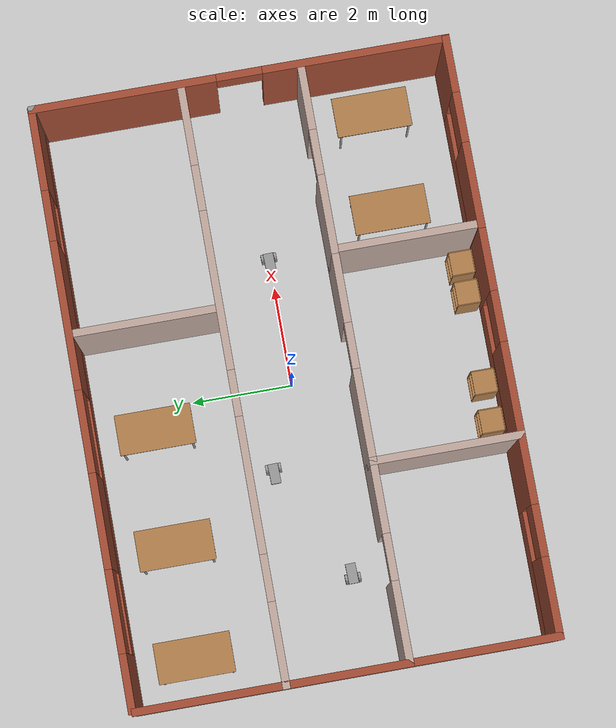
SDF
<sdf version="1.6">
 <world name="default">
  <plugin name="libhello_plugin" filename="libhello_plugin.so"/>
  <light name="sun" type="directional">
   <pose>0 0 10 0 -0 0</pose>
   <diffuse>0.8 0.8 0.8 1</diffuse>
   <specular>0.2 0.2 0.2 1</specular>
   <attenuation>
    <range>1000</range>
    <constant>0.9</constant>
    <linear>0.01</linear>
    <quadratic>0.001</quadratic>
   </attenuation>
   <direction>-0.5 0.1 -0.9</direction>
  </light>
  <model name="ground_plane">
   <static>1</static>
   <link name="link">
    <collision name="collision">
     <geometry><plane><normal>0 0 1</normal><size>100 100</size></plane></geometry>
     <surface><friction><ode><mu>100</mu><mu2>50</mu2></ode></friction></surface>
    </collision>
    <visual name="visual">
     <cast_shadows>0</cast_shadows>
     <geometry><plane><normal>0 0 1</normal><size>100 100</size></plane></geometry>
     <material>
      <script><uri>file://media/materials/scripts/gazebo.material</uri><name>Gazebo/Grey</name></script>
     </material>
    </visual>
   </link>
  </model>
  <gravity>0 0 -9.8</gravity>
  <magnetic_field>6e-06 2.3e-05 -4.2e-05</magnetic_field>
  <atmosphere type="adiabatic"/>
  <physics name="default_physics" default="0" type="ode">
   <max_step_size>0.001</max_step_size>
   <real_time_factor>1</real_time_factor>
   <real_time_update_rate>1000</real_time_update_rate>
  </physics>
  <scene><ambient>0.4 0.4 0.4 1</ambient><background>0.7 0.7 0.7 1</background><shadows>1</shadows></scene>
  <spherical_coordinates>
   <surface_model>EARTH_WGS84</surface_model>
   <latitude_deg>0</latitude_deg>
   <longitude_deg>0</longitude_deg>
   <elevation>0</elevation>
   <heading_deg>0</heading_deg>
  </spherical_coordinates>
  <model name="building1">
   <link name="Wall_0">
    <pose>5.83622 -0.00604 0 0 0 -1.5708</pose>
    <visual name="Wall_0_Visual_0">
     <pose>-2.28969 0 1.25 0 -0 0</pose>
     <geometry><box><size>3.67061 0.15 2.5</size></box></geometry>
     <material>
      <script><uri>file://media/materials/scripts/gazebo.material</uri><name>Gazebo/Bricks</name></script>
      <ambient>1 1 1 1</ambient>
     </material>
     <meta><layer>0</layer></meta>
    </visual>
    <collision name="Wall_0_Collision_0">
     <geometry><box><size>3.67061 0.15 2.5</size></box></geometry>
     <pose>-2.28969 0 1.25 0 -0 0</pose>
    </collision>
    <visual name="Wall_0_Visual_1">
     <pose>2.28531 0 1.25 0 -0 0</pose>
     <geometry><box><size>3.67939 0.15 2.5</size></box></geometry>
     <material>
      <script><uri>file://media/materials/scripts/gazebo.material</uri><name>Gazebo/Bricks</name></script>
      <ambient>1 1 1 1</ambient>
     </material>
     <meta><layer>0</layer></meta>
    </visual>
    <collision name="Wall_0_Collision_1">
     <geometry><box><size>3.67939 0.15 2.5</size></box></geometry>
     <pose>2.28531 0 1.25 0 -0 0</pose>
    </collision>
    <visual name="Wall_0_Visual_2">
     <pose>-0.004386 0 2.25 0 -0 0</pose>
     <geometry><box><size>0.9 0.15 0.5</size></box></geometry>
     <material>
      <script><uri>file://media/materials/scripts/gazebo.material</uri><name>Gazebo/Bricks</name></script>
      <ambient>1 1 1 1</ambient>
     </material>
     <meta><layer>0</layer></meta>
    </visual>
    <collision name="Wall_0_Collision_2">
     <geometry><box><size>0.9 0.15 0.5</size></box></geometry>
     <pose>-0.004386 0 2.25 0 -0 0</pose>
    </collision>
   </link>
   <link name="Wall_11">
    <pose>-3.91122 -4.05604 0 0 -0 3.14159</pose>
    <visual name="Wall_11_Visual_0">
     <pose>-1.29336 0 1.25 0 -0 0</pose>
     <geometry><box><size>1.41328 0.15 2.5</size></box></geometry>
     <material>
      <script><uri>file://media/materials/scripts/gazebo.material</uri><name>Gazebo/Bricks</name></script>
      <ambient>1 1 1 1</ambient>
     </material>
     <meta><layer>0</layer></meta>
    </visual>
    <collision name="Wall_11_Collision_0">
     <geometry><box><size>1.41328 0.15 2.5</size></box></geometry>
     <pose>-1.29336 0 1.25 0 -0 0</pose>
    </collision>
    <visual name="Wall_11_Visual_1">
     <pose>0.706639 0 0.375 0 -0 0</pose>
     <geometry><box><size>2.58672 0.15 0.75</size></box></geometry>
     <material>
      <script><uri>file://media/materials/scripts/gazebo.material</uri><name>Gazebo/Bricks</name></script>
      <ambient>1 1 1 1</ambient>
     </material>
     <meta><layer>0</layer></meta>
    </visual>
    <collision name="Wall_11_Collision_1">
     <geometry><box><size>2.58672 0.15 0.75</size></box></geometry>
     <pose>0.706639 0 0.375 0 -0 0</pose>
    </collision>
    <visual name="Wall_11_Visual_2">
     <pose>1.20664 0 1.625 0 -0 0</pose>
     <geometry><box><size>1.58672 0.15 1.75</size></box></geometry>
     <material>
      <script><uri>file://media/materials/scripts/gazebo.material</uri><name>Gazebo/Bricks</name></script>
      <ambient>1 1 1 1</ambient>
     </material>
     <meta><layer>0</layer></meta>
    </visual>
    <collision name="Wall_11_Collision_2">
     <geometry><box><size>1.58672 0.15 1.75</size></box></geometry>
     <pose>1.20664 0 1.625 0 -0 0</pose>
    </collision>
    <visual name="Wall_11_Visual_3">
     <pose>-0.086722 0 2.025 0 -0 0</pose>
     <geometry><box><size>1 0.15 0.95</size></box></geometry>
     <material>
      <script><uri>file://media/materials/scripts/gazebo.material</uri><name>Gazebo/Bricks</name></script>
      <ambient>1 1 1 1</ambient>
     </material>
     <meta><layer>0</layer></meta>
    </visual>
    <collision name="Wall_11_Collision_3">
     <geometry><box><size>1 0.15 0.95</size></box></geometry>
     <pose>-0.086722 0 2.025 0 -0 0</pose>
    </collision>
   </link>
   <link name="Wall_12">
    <collision name="Wall_12_Collision">
     <geometry><box><size>3 0.15 2.5</size></box></geometry>
     <pose>0 0 1.25 0 -0 0</pose>
    </collision>
    <visual name="Wall_12_Visual">
     <pose>0 0 1.25 0 -0 0</pose>
     <geometry><box><size>3 0.15 2.5</size></box></geometry>
     <material>
      <script><uri>file://media/materials/scripts/gazebo.material</uri><name>Gazebo/Bricks</name></script>
      <ambient>1 1 1 1</ambient>
     </material>
     <meta><layer>0</layer></meta>
    </visual>
    <pose>-5.83622 -2.63104 0 0 -0 1.5708</pose>
   </link>
   <link name="Wall_13">
    <pose>-3.91122 -1.20604 0 0 -0 0</pose>
    <visual name="Wall_13_Visual_0">
     <pose>-1.18164 0 1.25 0 -0 0</pose>
     <geometry><box><size>1.63672 0.15 2.5</size></box></geometry>
     <material>
      <script><uri>file://media/materials/scripts/gazebo.material</uri><name>Gazebo/Grey</name></script>
      <ambient>0.760784 0.662745 0.627451 1</ambient>
     </material>
     <meta><layer>0</layer></meta>
    </visual>
    <collision name="Wall_13_Collision_0">
     <geometry><box><size>1.63672 0.15 2.5</size></box></geometry>
     <pose>-1.18164 0 1.25 0 -0 0</pose>
    </collision>
    <visual name="Wall_13_Visual_1">
     <pose>1.26836 0 1.25 0 -0 0</pose>
     <geometry><box><size>1.46328 0.15 2.5</size></box></geometry>
     <material>
      <script><uri>file://media/materials/scripts/gazebo.material</uri><name>Gazebo/Grey</name></script>
      <ambient>0.760784 0.662745 0.627451 1</ambient>
     </material>
     <meta><layer>0</layer></meta>
    </visual>
    <collision name="Wall_13_Collision_1">
     <geometry><box><size>1.46328 0.15 2.5</size></box></geometry>
     <pose>1.26836 0 1.25 0 -0 0</pose>
    </collision>
    <visual name="Wall_13_Visual_2">
     <pose>0.086722 0 2.25 0 -0 0</pose>
     <geometry><box><size>0.9 0.15 0.5</size></box></geometry>
     <material>
      <script><uri>file://media/materials/scripts/gazebo.material</uri><name>Gazebo/Grey</name></script>
      <ambient>0.760784 0.662745 0.627451 1</ambient>
     </material>
     <meta><layer>0</layer></meta>
    </visual>
    <collision name="Wall_13_Collision_2">
     <geometry><box><size>0.9 0.15 0.5</size></box></geometry>
     <pose>0.086722 0 2.25 0 -0 0</pose>
    </collision>
   </link>
   <link name="Wall_15">
    <collision name="Wall_15_Collision">
     <geometry><box><size>2.5 0.15 2.5</size></box></geometry>
     <pose>0 0 1.25 0 -0 0</pose>
    </collision>
    <visual name="Wall_15_Visual">
     <pose>0 0 1.25 0 -0 0</pose>
     <geometry><box><size>2.5 0.15 2.5</size></box></geometry>
     <material>
      <script><uri>file://media/materials/scripts/gazebo.material</uri><name>Gazebo/Bricks</name></script>
      <ambient>1 1 1 1</ambient>
     </material>
     <meta><layer>0</layer></meta>
    </visual>
    <pose>-5.83622 -0.03104 0 0 -0 1.5708</pose>
   </link>
   <link name="Wall_16">
    <pose>-0.036216 1.14396 0 0 -0 0</pose>
    <visual name="Wall_16_Visual_0">
     <pose>-5.04789 0 1.25 0 -0 0</pose>
     <geometry><box><size>1.65421 0.15 2.5</size></box></geometry>
     <material>
      <script><uri>file://media/materials/scripts/gazebo.material</uri><name>Gazebo/Grey</name></script>
      <ambient>0.760784 0.662745 0.627451 1</ambient>
     </material>
     <meta><layer>0</layer></meta>
    </visual>
    <collision name="Wall_16_Collision_0">
     <geometry><box><size>1.65421 0.15 2.5</size></box></geometry>
     <pose>-5.04789 0 1.25 0 -0 0</pose>
    </collision>
    <visual name="Wall_16_Visual_1">
     <pose>-1.99555 0 1.25 0 -0 0</pose>
     <geometry><box><size>2.65048 0.15 2.5</size></box></geometry>
     <material>
      <script><uri>file://media/materials/scripts/gazebo.material</uri><name>Gazebo/Grey</name></script>
      <ambient>0.760784 0.662745 0.627451 1</ambient>
     </material>
     <meta><layer>0</layer></meta>
    </visual>
    <collision name="Wall_16_Collision_1">
     <geometry><box><size>2.65048 0.15 2.5</size></box></geometry>
     <pose>-1.99555 0 1.25 0 -0 0</pose>
    </collision>
    <visual name="Wall_16_Visual_2">
     <pose>1.79105 0 1.25 0 -0 0</pose>
     <geometry><box><size>3.12271 0.15 2.5</size></box></geometry>
     <material>
      <script><uri>file://media/materials/scripts/gazebo.material</uri><name>Gazebo/Grey</name></script>
      <ambient>0.760784 0.662745 0.627451 1</ambient>
     </material>
     <meta><layer>0</layer></meta>
    </visual>
    <collision name="Wall_16_Collision_2">
     <geometry><box><size>3.12271 0.15 2.5</size></box></geometry>
     <pose>1.79105 0 1.25 0 -0 0</pose>
    </collision>
    <visual name="Wall_16_Visual_3">
     <pose>5.0637 0 1.25 0 -0 0</pose>
     <geometry><box><size>1.62259 0.15 2.5</size></box></geometry>
     <material>
      <script><uri>file://media/materials/scripts/gazebo.material</uri><name>Gazebo/Grey</name></script>
      <ambient>0.760784 0.662745 0.627451 1</ambient>
     </material>
     <meta><layer>0</layer></meta>
    </visual>
    <collision name="Wall_16_Collision_3">
     <geometry><box><size>1.62259 0.15 2.5</size></box></geometry>
     <pose>5.0637 0 1.25 0 -0 0</pose>
    </collision>
    <visual name="Wall_16_Visual_4">
     <pose>-3.77079 0 2.25 0 -0 0</pose>
     <geometry><box><size>0.9 0.15 0.5</size></box></geometry>
     <material>
      <script><uri>file://media/materials/scripts/gazebo.material</uri><name>Gazebo/Grey</name></script>
      <ambient>0.760784 0.662745 0.627451 1</ambient>
     </material>
     <meta><layer>0</layer></meta>
    </visual>
    <collision name="Wall_16_Collision_4">
     <geometry><box><size>0.9 0.15 0.5</size></box></geometry>
     <pose>-3.77079 0 2.25 0 -0 0</pose>
    </collision>
    <visual name="Wall_16_Visual_5">
     <pose>-0.220305 0 2.25 0 -0 0</pose>
     <geometry><box><size>0.9 0.15 0.5</size></box></geometry>
     <material>
      <script><uri>file://media/materials/scripts/gazebo.material</uri><name>Gazebo/Grey</name></script>
      <ambient>0.760784 0.662745 0.627451 1</ambient>
     </material>
     <meta><layer>0</layer></meta>
    </visual>
    <collision name="Wall_16_Collision_5">
     <geometry><box><size>0.9 0.15 0.5</size></box></geometry>
     <pose>-0.220305 0 2.25 0 -0 0</pose>
    </collision>
    <visual name="Wall_16_Visual_6">
     <pose>3.80241 0 2.25 0 -0 0</pose>
     <geometry><box><size>0.9 0.15 0.5</size></box></geometry>
     <material>
      <script><uri>file://media/materials/scripts/gazebo.material</uri><name>Gazebo/Grey</name></script>
      <ambient>0.760784 0.662745 0.627451 1</ambient>
     </material>
     <meta><layer>0</layer></meta>
    </visual>
    <collision name="Wall_16_Collision_6">
     <geometry><box><size>0.9 0.15 0.5</size></box></geometry>
     <pose>3.80241 0 2.25 0 -0 0</pose>
    </collision>
   </link>
   <link name="Wall_22">
    <collision name="Wall_22_Collision">
     <geometry><box><size>3 0.15 2.5</size></box></geometry>
     <pose>0 0 1.25 0 -0 0</pose>
    </collision>
    <visual name="Wall_22_Visual">
     <pose>0 0 1.25 0 -0 0</pose>
     <geometry><box><size>3 0.15 2.5</size></box></geometry>
     <material>
      <script><uri>file://media/materials/scripts/gazebo.material</uri><name>Gazebo/Bricks</name></script>
      <ambient>1 1 1 1</ambient>
     </material>
     <meta><layer>0</layer></meta>
    </visual>
    <pose>-5.83622 2.56896 0 0 -0 1.5708</pose>
   </link>
   <link name="Wall_24">
    <collision name="Wall_24_Collision">
     <geometry><box><size>0.15 0.15 2.5</size></box></geometry>
     <pose>0 0 1.25 0 -0 0</pose>
    </collision>
    <visual name="Wall_24_Visual">
     <pose>0 0 1.25 0 -0 0</pose>
     <geometry><box><size>0.15 0.15 2.5</size></box></geometry>
     <material>
      <script><uri>file://media/materials/scripts/gazebo.material</uri><name>Gazebo/Grey</name></script>
      <ambient>1 1 1 1</ambient>
     </material>
     <meta><layer>0</layer></meta>
    </visual>
    <pose>5.83622 4.04396 0 0 -0 0</pose>
   </link>
   <link name="Wall_28">
    <pose>-0.000871 4.05604 0 0 -0 0</pose>
    <visual name="Wall_28_Visual_0">
     <pose>-5.30178 0 1.25 0 -0 0</pose>
     <geometry><box><size>1.14644 0.15 2.5</size></box></geometry>
     <material>
      <script><uri>file://media/materials/scripts/gazebo.material</uri><name>Gazebo/Bricks</name></script>
      <ambient>1 1 1 1</ambient>
     </material>
     <meta><layer>0</layer></meta>
    </visual>
    <collision name="Wall_28_Collision_0">
     <geometry><box><size>1.14644 0.15 2.5</size></box></geometry>
     <pose>-5.30178 0 1.25 0 -0 0</pose>
    </collision>
    <visual name="Wall_28_Visual_1">
     <pose>0.573218 0 0.375 0 -0 0</pose>
     <geometry><box><size>10.6036 0.15 0.75</size></box></geometry>
     <material>
      <script><uri>file://media/materials/scripts/gazebo.material</uri><name>Gazebo/Bricks</name></script>
      <ambient>1 1 1 1</ambient>
     </material>
     <meta><layer>0</layer></meta>
    </visual>
    <collision name="Wall_28_Collision_1">
     <geometry><box><size>10.6036 0.15 0.75</size></box></geometry>
     <pose>0.573218 0 0.375 0 -0 0</pose>
    </collision>
    <visual name="Wall_28_Visual_2">
     <pose>-2.20579 0 1.625 0 -0 0</pose>
     <geometry><box><size>1.84554 0.15 1.75</size></box></geometry>
     <material>
      <script><uri>file://media/materials/scripts/gazebo.material</uri><name>Gazebo/Bricks</name></script>
      <ambient>1 1 1 1</ambient>
     </material>
     <meta><layer>0</layer></meta>
    </visual>
    <collision name="Wall_28_Collision_2">
     <geometry><box><size>1.84554 0.15 1.75</size></box></geometry>
     <pose>-2.20579 0 1.625 0 -0 0</pose>
    </collision>
    <visual name="Wall_28_Visual_3">
     <pose>1.77453 0 1.625 0 -0 0</pose>
     <geometry><box><size>2.91511 0.15 1.75</size></box></geometry>
     <material>
      <script><uri>file://media/materials/scripts/gazebo.material</uri><name>Gazebo/Bricks</name></script>
      <ambient>1 1 1 1</ambient>
     </material>
     <meta><layer>0</layer></meta>
    </visual>
    <collision name="Wall_28_Collision_3">
     <geometry><box><size>2.91511 0.15 1.75</size></box></geometry>
     <pose>1.77453 0 1.625 0 -0 0</pose>
    </collision>
    <visual name="Wall_28_Visual_4">
     <pose>5.05354 0 1.625 0 -0 0</pose>
     <geometry><box><size>1.64292 0.15 1.75</size></box></geometry>
     <material>
      <script><uri>file://media/materials/scripts/gazebo.material</uri><name>Gazebo/Bricks</name></script>
      <ambient>1 1 1 1</ambient>
     </material>
     <meta><layer>0</layer></meta>
    </visual>
    <collision name="Wall_28_Collision_4">
     <geometry><box><size>1.64292 0.15 1.75</size></box></geometry>
     <pose>5.05354 0 1.625 0 -0 0</pose>
    </collision>
    <visual name="Wall_28_Visual_5">
     <pose>-3.92856 0 2.025 0 -0 0</pose>
     <geometry><box><size>1.6 0.15 0.95</size></box></geometry>
     <material>
      <script><uri>file://media/materials/scripts/gazebo.material</uri><name>Gazebo/Bricks</name></script>
      <ambient>1 1 1 1</ambient>
     </material>
     <meta><layer>0</layer></meta>
    </visual>
    <collision name="Wall_28_Collision_5">
     <geometry><box><size>1.6 0.15 0.95</size></box></geometry>
     <pose>-3.92856 0 2.025 0 -0 0</pose>
    </collision>
    <visual name="Wall_28_Visual_6">
     <pose>-0.483021 0 2.025 0 -0 0</pose>
     <geometry><box><size>1.6 0.15 0.95</size></box></geometry>
     <material>
      <script><uri>file://media/materials/scripts/gazebo.material</uri><name>Gazebo/Bricks</name></script>
      <ambient>1 1 1 1</ambient>
     </material>
     <meta><layer>0</layer></meta>
    </visual>
    <collision name="Wall_28_Collision_6">
     <geometry><box><size>1.6 0.15 0.95</size></box></geometry>
     <pose>-0.483021 0 2.025 0 -0 0</pose>
    </collision>
    <visual name="Wall_28_Visual_7">
     <pose>3.73208 0 2.025 0 -0 0</pose>
     <geometry><box><size>1 0.15 0.95</size></box></geometry>
     <material>
      <script><uri>file://media/materials/scripts/gazebo.material</uri><name>Gazebo/Bricks</name></script>
      <ambient>1 1 1 1</ambient>
     </material>
     <meta><layer>0</layer></meta>
    </visual>
    <collision name="Wall_28_Collision_7">
     <geometry><box><size>1 0.15 0.95</size></box></geometry>
     <pose>3.73208 0 2.025 0 -0 0</pose>
    </collision>
   </link>
   <link name="Wall_3">
    <pose>3.97243 -4.05604 0 0 -0 3.14159</pose>
    <visual name="Wall_3_Visual_0">
     <pose>-1.35239 0 1.25 0 -0 0</pose>
     <geometry><box><size>1.13781 0.15 2.5</size></box></geometry>
     <material>
      <script><uri>file://media/materials/scripts/gazebo.material</uri><name>Gazebo/Bricks</name></script>
      <ambient>1 1 1 1</ambient>
     </material>
     <meta><layer>0</layer></meta>
    </visual>
    <collision name="Wall_3_Collision_0">
     <geometry><box><size>1.13781 0.15 2.5</size></box></geometry>
     <pose>-1.35239 0 1.25 0 -0 0</pose>
    </collision>
    <visual name="Wall_3_Visual_1">
     <pose>0.568905 0 0.375 0 -0 0</pose>
     <geometry><box><size>2.70478 0.15 0.75</size></box></geometry>
     <material>
      <script><uri>file://media/materials/scripts/gazebo.material</uri><name>Gazebo/Bricks</name></script>
      <ambient>1 1 1 1</ambient>
     </material>
     <meta><layer>0</layer></meta>
    </visual>
    <collision name="Wall_3_Collision_1">
     <geometry><box><size>2.70478 0.15 0.75</size></box></geometry>
     <pose>0.568905 0 0.375 0 -0 0</pose>
    </collision>
    <visual name="Wall_3_Visual_2">
     <pose>1.0689 0 1.625 0 -0 0</pose>
     <geometry><box><size>1.70478 0.15 1.75</size></box></geometry>
     <material>
      <script><uri>file://media/materials/scripts/gazebo.material</uri><name>Gazebo/Bricks</name></script>
      <ambient>1 1 1 1</ambient>
     </material>
     <meta><layer>0</layer></meta>
    </visual>
    <collision name="Wall_3_Collision_2">
     <geometry><box><size>1.70478 0.15 1.75</size></box></geometry>
     <pose>1.0689 0 1.625 0 -0 0</pose>
    </collision>
    <visual name="Wall_3_Visual_3">
     <pose>-0.283484 0 2.025 0 -0 0</pose>
     <geometry><box><size>1 0.15 0.95</size></box></geometry>
     <material>
      <script><uri>file://media/materials/scripts/gazebo.material</uri><name>Gazebo/Bricks</name></script>
      <ambient>1 1 1 1</ambient>
     </material>
     <meta><layer>0</layer></meta>
    </visual>
    <collision name="Wall_3_Collision_3">
     <geometry><box><size>1 0.15 0.95</size></box></geometry>
     <pose>-0.283484 0 2.025 0 -0 0</pose>
    </collision>
   </link>
   <link name="Wall_30">
    <collision name="Wall_30_Collision">
     <geometry><box><size>3 0.15 2.5</size></box></geometry>
     <pose>0 0 1.25 0 -0 0</pose>
    </collision>
    <visual name="Wall_30_Visual">
     <pose>0 0 1.25 0 -0 0</pose>
     <geometry><box><size>3 0.15 2.5</size></box></geometry>
     <material>
      <script><uri>file://media/materials/scripts/gazebo.material</uri><name>Gazebo/Grey</name></script>
      <ambient>0.760784 0.662745 0.627451 1</ambient>
     </material>
     <meta><layer>0</layer></meta>
    </visual>
    <pose>1.40504 2.59518 0 0 -0 1.5708</pose>
   </link>
   <link name="Wall_4">
    <collision name="Wall_4_Collision">
     <geometry><box><size>3 0.15 2.5</size></box></geometry>
     <pose>0 0 1.25 0 -0 0</pose>
    </collision>
    <visual name="Wall_4_Visual">
     <pose>0 0 1.25 0 -0 0</pose>
     <geometry><box><size>3 0.15 2.5</size></box></geometry>
     <material>
      <script><uri>file://media/materials/scripts/gazebo.material</uri><name>Gazebo/Grey</name></script>
      <ambient>0.760784 0.662745 0.627451 1</ambient>
     </material>
     <meta><layer>0</layer></meta>
    </visual>
    <pose>2.14363 -2.63104 0 0 -0 1.5708</pose>
   </link>
   <link name="Wall_5">
    <pose>3.91996 -1.20604 0 0 -0 0</pose>
    <visual name="Wall_5_Visual_0">
     <pose>-1.08763 0 1.25 0 -0 0</pose>
     <geometry><box><size>1.56239 0.15 2.5</size></box></geometry>
     <material>
      <script><uri>file://media/materials/scripts/gazebo.material</uri><name>Gazebo/Grey</name></script>
      <ambient>0.760784 0.662745 0.627451 1</ambient>
     </material>
     <meta><layer>0</layer></meta>
    </visual>
    <collision name="Wall_5_Collision_0">
     <geometry><box><size>1.56239 0.15 2.5</size></box></geometry>
     <pose>-1.08763 0 1.25 0 -0 0</pose>
    </collision>
    <visual name="Wall_5_Visual_1">
     <pose>1.23119 0 1.25 0 -0 0</pose>
     <geometry><box><size>1.27526 0.15 2.5</size></box></geometry>
     <material>
      <script><uri>file://media/materials/scripts/gazebo.material</uri><name>Gazebo/Grey</name></script>
      <ambient>0.760784 0.662745 0.627451 1</ambient>
     </material>
     <meta><layer>0</layer></meta>
    </visual>
    <collision name="Wall_5_Collision_1">
     <geometry><box><size>1.27526 0.15 2.5</size></box></geometry>
     <pose>1.23119 0 1.25 0 -0 0</pose>
    </collision>
    <visual name="Wall_5_Visual_2">
     <pose>0.143564 0 2.25 0 -0 0</pose>
     <geometry><box><size>0.9 0.15 0.5</size></box></geometry>
     <material>
      <script><uri>file://media/materials/scripts/gazebo.material</uri><name>Gazebo/Grey</name></script>
      <ambient>0.760784 0.662745 0.627451 1</ambient>
     </material>
     <meta><layer>0</layer></meta>
    </visual>
    <collision name="Wall_5_Collision_2">
     <geometry><box><size>0.9 0.15 0.5</size></box></geometry>
     <pose>0.143564 0 2.25 0 -0 0</pose>
    </collision>
   </link>
   <link name="Wall_7">
    <pose>0.06996 -4.05604 0 0 -0 3.14159</pose>
    <visual name="Wall_7_Visual_0">
     <pose>-1.44093 0 1.25 0 -0 0</pose>
     <geometry><box><size>1.38048 0.15 2.5</size></box></geometry>
     <material>
      <script><uri>file://media/materials/scripts/gazebo.material</uri><name>Gazebo/Bricks</name></script>
      <ambient>1 1 1 1</ambient>
     </material>
     <meta><layer>0</layer></meta>
    </visual>
    <collision name="Wall_7_Collision_0">
     <geometry><box><size>1.38048 0.15 2.5</size></box></geometry>
     <pose>-1.44093 0 1.25 0 -0 0</pose>
    </collision>
    <visual name="Wall_7_Visual_1">
     <pose>0.690242 0 0.375 0 -0 0</pose>
     <geometry><box><size>2.88187 0.15 0.75</size></box></geometry>
     <material>
      <script><uri>file://media/materials/scripts/gazebo.material</uri><name>Gazebo/Bricks</name></script>
      <ambient>1 1 1 1</ambient>
     </material>
     <meta><layer>0</layer></meta>
    </visual>
    <collision name="Wall_7_Collision_1">
     <geometry><box><size>2.88187 0.15 0.75</size></box></geometry>
     <pose>0.690242 0 0.375 0 -0 0</pose>
    </collision>
    <visual name="Wall_7_Visual_2">
     <pose>1.19024 0 1.625 0 -0 0</pose>
     <geometry><box><size>1.88187 0.15 1.75</size></box></geometry>
     <material>
      <script><uri>file://media/materials/scripts/gazebo.material</uri><name>Gazebo/Bricks</name></script>
      <ambient>1 1 1 1</ambient>
     </material>
     <meta><layer>0</layer></meta>
    </visual>
    <collision name="Wall_7_Collision_2">
     <geometry><box><size>1.88187 0.15 1.75</size></box></geometry>
     <pose>1.19024 0 1.625 0 -0 0</pose>
    </collision>
    <visual name="Wall_7_Visual_3">
     <pose>-0.250691 0 2.025 0 -0 0</pose>
     <geometry><box><size>1 0.15 0.95</size></box></geometry>
     <material>
      <script><uri>file://media/materials/scripts/gazebo.material</uri><name>Gazebo/Bricks</name></script>
      <ambient>1 1 1 1</ambient>
     </material>
     <meta><layer>0</layer></meta>
    </visual>
    <collision name="Wall_7_Collision_3">
     <geometry><box><size>1 0.15 0.95</size></box></geometry>
     <pose>-0.250691 0 2.025 0 -0 0</pose>
    </collision>
   </link>
   <link name="Wall_8">
    <collision name="Wall_8_Collision">
     <geometry><box><size>3 0.15 2.5</size></box></geometry>
     <pose>0 0 1.25 0 -0 0</pose>
    </collision>
    <visual name="Wall_8_Visual">
     <pose>0 0 1.25 0 -0 0</pose>
     <geometry><box><size>3 0.15 2.5</size></box></geometry>
     <material>
      <script><uri>file://media/materials/scripts/gazebo.material</uri><name>Gazebo/Grey</name></script>
      <ambient>0.760784 0.662745 0.627451 1</ambient>
     </material>
     <meta><layer>0</layer></meta>
    </visual>
    <pose>-1.98622 -2.63104 0 0 -0 1.5708</pose>
   </link>
   <link name="Wall_9">
    <pose>0.06996 -1.20604 0 0 -0 0</pose>
    <visual name="Wall_9_Visual_0">
     <pose>-1.20022 0 1.25 0 -0 0</pose>
     <geometry><box><size>1.86191 0.15 2.5</size></box></geometry>
     <material>
      <script><uri>file://media/materials/scripts/gazebo.material</uri><name>Gazebo/Grey</name></script>
      <ambient>0.760784 0.662745 0.627451 1</ambient>
     </material>
     <meta><layer>0</layer></meta>
    </visual>
    <collision name="Wall_9_Collision_0">
     <geometry><box><size>1.86191 0.15 2.5</size></box></geometry>
     <pose>-1.20022 0 1.25 0 -0 0</pose>
    </collision>
    <visual name="Wall_9_Visual_1">
     <pose>1.38095 0 1.25 0 -0 0</pose>
     <geometry><box><size>1.50045 0.15 2.5</size></box></geometry>
     <material>
      <script><uri>file://media/materials/scripts/gazebo.material</uri><name>Gazebo/Grey</name></script>
      <ambient>0.760784 0.662745 0.627451 1</ambient>
     </material>
     <meta><layer>0</layer></meta>
    </visual>
    <collision name="Wall_9_Collision_1">
     <geometry><box><size>1.50045 0.15 2.5</size></box></geometry>
     <pose>1.38095 0 1.25 0 -0 0</pose>
    </collision>
    <visual name="Wall_9_Visual_2">
     <pose>0.180731 0 2.25 0 -0 0</pose>
     <geometry><box><size>0.9 0.15 0.5</size></box></geometry>
     <material>
      <script><uri>file://media/materials/scripts/gazebo.material</uri><name>Gazebo/Grey</name></script>
      <ambient>0.760784 0.662745 0.627451 1</ambient>
     </material>
     <meta><layer>0</layer></meta>
    </visual>
    <collision name="Wall_9_Collision_2">
     <geometry><box><size>0.9 0.15 0.5</size></box></geometry>
     <pose>0.180731 0 2.25 0 -0 0</pose>
    </collision>
   </link>
   <static>1</static>
  </model>
  <model name="table">
   <static>1</static>
   <link name="link">
    <collision name="surface">
     <pose>0 0 1 0 -0 0</pose>
     <geometry><box><size>1.5 0.8 0.03</size></box></geometry>
     <surface><friction><ode><mu>0.6</mu><mu2>0.6</mu2></ode></friction></surface>
    </collision>
    <visual name="visual1">
     <pose>0 0 1 0 -0 0</pose>
     <geometry><box><size>1.5 0.8 0.03</size></box></geometry>
     <material>
      <script><uri>file://media/materials/scripts/gazebo.material</uri><name>Gazebo/Wood</name></script>
     </material>
    </visual>
    <collision name="front_left_leg">
     <pose>0.68 0.38 0.5 0 -0 0</pose>
     <geometry><cylinder><radius>0.02</radius><length>1</length></cylinder></geometry>
    </collision>
    <visual name="front_left_leg">
     <pose>0.68 0.38 0.5 0 -0 0</pose>
     <geometry><cylinder><radius>0.02</radius><length>1</length></cylinder></geometry>
     <material>
      <script><uri>file://media/materials/scripts/gazebo.material</uri><name>Gazebo/Grey</name></script>
     </material>
    </visual>
    <collision name="front_right_leg">
     <pose>0.68 -0.38 0.5 0 -0 0</pose>
     <geometry><cylinder><radius>0.02</radius><length>1</length></cylinder></geometry>
    </collision>
    <visual name="front_right_leg">
     <pose>0.68 -0.38 0.5 0 -0 0</pose>
     <geometry><cylinder><radius>0.02</radius><length>1</length></cylinder></geometry>
     <material>
      <script><uri>file://media/materials/scripts/gazebo.material</uri><name>Gazebo/Grey</name></script>
     </material>
    </visual>
    <collision name="back_right_leg">
     <pose>-0.68 -0.38 0.5 0 -0 0</pose>
     <geometry><cylinder><radius>0.02</radius><length>1</length></cylinder></geometry>
    </collision>
    <visual name="back_right_leg">
     <pose>-0.68 -0.38 0.5 0 -0 0</pose>
     <geometry><cylinder><radius>0.02</radius><length>1</length></cylinder></geometry>
     <material>
      <script><uri>file://media/materials/scripts/gazebo.material</uri><name>Gazebo/Grey</name></script>
     </material>
    </visual>
    <collision name="back_left_leg">
     <pose>-0.68 0.38 0.5 0 -0 0</pose>
     <geometry><cylinder><radius>0.02</radius><length>1</length></cylinder></geometry>
    </collision>
    <visual name="back_left_leg">
     <pose>-0.68 0.38 0.5 0 -0 0</pose>
     <geometry><cylinder><radius>0.02</radius><length>1</length></cylinder></geometry>
     <material>
      <script><uri>file://media/materials/scripts/gazebo.material</uri><name>Gazebo/Grey</name></script>
     </material>
    </visual>
   </link>
   <pose>-0.5 2.8 0 0 -0 1.5707</pose>
  </model>
  <model name="table_clone">
   <static>1</static>
   <link name="link">
    <collision name="surface">
     <pose>0 0 1 0 -0 0</pose>
     <geometry><box><size>1.5 0.8 0.03</size></box></geometry>
     <surface><friction><ode><mu>0.6</mu><mu2>0.6</mu2></ode></friction></surface>
    </collision>
    <visual name="visual1">
     <pose>0 0 1 0 -0 0</pose>
     <geometry><box><size>1.5 0.8 0.03</size></box></geometry>
     <material>
      <script><uri>file://media/materials/scripts/gazebo.material</uri><name>Gazebo/Wood</name></script>
     </material>
    </visual>
    <collision name="front_left_leg">
     <pose>0.68 0.38 0.5 0 -0 0</pose>
     <geometry><cylinder><radius>0.02</radius><length>1</length></cylinder></geometry>
    </collision>
    <visual name="front_left_leg">
     <pose>0.68 0.38 0.5 0 -0 0</pose>
     <geometry><cylinder><radius>0.02</radius><length>1</length></cylinder></geometry>
     <material>
      <script><uri>file://media/materials/scripts/gazebo.material</uri><name>Gazebo/Grey</name></script>
     </material>
    </visual>
    <collision name="front_right_leg">
     <pose>0.68 -0.38 0.5 0 -0 0</pose>
     <geometry><cylinder><radius>0.02</radius><length>1</length></cylinder></geometry>
    </collision>
    <visual name="front_right_leg">
     <pose>0.68 -0.38 0.5 0 -0 0</pose>
     <geometry><cylinder><radius>0.02</radius><length>1</length></cylinder></geometry>
     <material>
      <script><uri>file://media/materials/scripts/gazebo.material</uri><name>Gazebo/Grey</name></script>
     </material>
    </visual>
    <collision name="back_right_leg">
     <pose>-0.68 -0.38 0.5 0 -0 0</pose>
     <geometry><cylinder><radius>0.02</radius><length>1</length></cylinder></geometry>
    </collision>
    <visual name="back_right_leg">
     <pose>-0.68 -0.38 0.5 0 -0 0</pose>
     <geometry><cylinder><radius>0.02</radius><length>1</length></cylinder></geometry>
     <material>
      <script><uri>file://media/materials/scripts/gazebo.material</uri><name>Gazebo/Grey</name></script>
     </material>
    </visual>
    <collision name="back_left_leg">
     <pose>-0.68 0.38 0.5 0 -0 0</pose>
     <geometry><cylinder><radius>0.02</radius><length>1</length></cylinder></geometry>
    </collision>
    <visual name="back_left_leg">
     <pose>-0.68 0.38 0.5 0 -0 0</pose>
     <geometry><cylinder><radius>0.02</radius><length>1</length></cylinder></geometry>
     <material>
      <script><uri>file://media/materials/scripts/gazebo.material</uri><name>Gazebo/Grey</name></script>
     </material>
    </visual>
   </link>
   <pose>-2.8 2.8 0 0 -0 1.5707</pose>
  </model>
  <model name="table_clone_0">
   <static>1</static>
   <link name="link">
    <collision name="surface">
     <pose>0 0 1 0 -0 0</pose>
     <geometry><box><size>1.5 0.8 0.03</size></box></geometry>
     <surface><friction><ode><mu>0.6</mu><mu2>0.6</mu2></ode></friction></surface>
    </collision>
    <visual name="visual1">
     <pose>0 0 1 0 -0 0</pose>
     <geometry><box><size>1.5 0.8 0.03</size></box></geometry>
     <material>
      <script><uri>file://media/materials/scripts/gazebo.material</uri><name>Gazebo/Wood</name></script>
     </material>
    </visual>
    <collision name="front_left_leg">
     <pose>0.68 0.38 0.5 0 -0 0</pose>
     <geometry><cylinder><radius>0.02</radius><length>1</length></cylinder></geometry>
    </collision>
    <visual name="front_left_leg">
     <pose>0.68 0.38 0.5 0 -0 0</pose>
     <geometry><cylinder><radius>0.02</radius><length>1</length></cylinder></geometry>
     <material>
      <script><uri>file://media/materials/scripts/gazebo.material</uri><name>Gazebo/Grey</name></script>
     </material>
    </visual>
    <collision name="front_right_leg">
     <pose>0.68 -0.38 0.5 0 -0 0</pose>
     <geometry><cylinder><radius>0.02</radius><length>1</length></cylinder></geometry>
    </collision>
    <visual name="front_right_leg">
     <pose>0.68 -0.38 0.5 0 -0 0</pose>
     <geometry><cylinder><radius>0.02</radius><length>1</length></cylinder></geometry>
     <material>
      <script><uri>file://media/materials/scripts/gazebo.material</uri><name>Gazebo/Grey</name></script>
     </material>
    </visual>
    <collision name="back_right_leg">
     <pose>-0.68 -0.38 0.5 0 -0 0</pose>
     <geometry><cylinder><radius>0.02</radius><length>1</length></cylinder></geometry>
    </collision>
    <visual name="back_right_leg">
     <pose>-0.68 -0.38 0.5 0 -0 0</pose>
     <geometry><cylinder><radius>0.02</radius><length>1</length></cylinder></geometry>
     <material>
      <script><uri>file://media/materials/scripts/gazebo.material</uri><name>Gazebo/Grey</name></script>
     </material>
    </visual>
    <collision name="back_left_leg">
     <pose>-0.68 0.38 0.5 0 -0 0</pose>
     <geometry><cylinder><radius>0.02</radius><length>1</length></cylinder></geometry>
    </collision>
    <visual name="back_left_leg">
     <pose>-0.68 0.38 0.5 0 -0 0</pose>
     <geometry><cylinder><radius>0.02</radius><length>1</length></cylinder></geometry>
     <material>
      <script><uri>file://media/materials/scripts/gazebo.material</uri><name>Gazebo/Grey</name></script>
     </material>
    </visual>
   </link>
   <pose>-5.00107 2.8 0 0 -0 1.5707</pose>
  </model>
  <model name="table_clone_clone">
   <static>1</static>
   <link name="link">
    <collision name="surface">
     <pose>0 0 1 0 -0 0</pose>
     <geometry><box><size>1.5 0.8 0.03</size></box></geometry>
     <surface><friction><ode><mu>0.6</mu><mu2>0.6</mu2></ode></friction></surface>
    </collision>
    <visual name="visual1">
     <pose>0 0 1 0 -0 0</pose>
     <geometry><box><size>1.5 0.8 0.03</size></box></geometry>
     <material>
      <script><uri>file://media/materials/scripts/gazebo.material</uri><name>Gazebo/Wood</name></script>
     </material>
    </visual>
    <collision name="front_left_leg">
     <pose>0.68 0.38 0.5 0 -0 0</pose>
     <geometry><cylinder><radius>0.02</radius><length>1</length></cylinder></geometry>
    </collision>
    <visual name="front_left_leg">
     <pose>0.68 0.38 0.5 0 -0 0</pose>
     <geometry><cylinder><radius>0.02</radius><length>1</length></cylinder></geometry>
     <material>
      <script><uri>file://media/materials/scripts/gazebo.material</uri><name>Gazebo/Grey</name></script>
     </material>
    </visual>
    <collision name="front_right_leg">
     <pose>0.68 -0.38 0.5 0 -0 0</pose>
     <geometry><cylinder><radius>0.02</radius><length>1</length></cylinder></geometry>
    </collision>
    <visual name="front_right_leg">
     <pose>0.68 -0.38 0.5 0 -0 0</pose>
     <geometry><cylinder><radius>0.02</radius><length>1</length></cylinder></geometry>
     <material>
      <script><uri>file://media/materials/scripts/gazebo.material</uri><name>Gazebo/Grey</name></script>
     </material>
    </visual>
    <collision name="back_right_leg">
     <pose>-0.68 -0.38 0.5 0 -0 0</pose>
     <geometry><cylinder><radius>0.02</radius><length>1</length></cylinder></geometry>
    </collision>
    <visual name="back_right_leg">
     <pose>-0.68 -0.38 0.5 0 -0 0</pose>
     <geometry><cylinder><radius>0.02</radius><length>1</length></cylinder></geometry>
     <material>
      <script><uri>file://media/materials/scripts/gazebo.material</uri><name>Gazebo/Grey</name></script>
     </material>
    </visual>
    <collision name="back_left_leg">
     <pose>-0.68 0.38 0.5 0 -0 0</pose>
     <geometry><cylinder><radius>0.02</radius><length>1</length></cylinder></geometry>
    </collision>
    <visual name="back_left_leg">
     <pose>-0.68 0.38 0.5 0 -0 0</pose>
     <geometry><cylinder><radius>0.02</radius><length>1</length></cylinder></geometry>
     <material>
      <script><uri>file://media/materials/scripts/gazebo.material</uri><name>Gazebo/Grey</name></script>
     </material>
    </visual>
   </link>
   <pose>3 -2.5 0 0 -0 1.5707</pose>
  </model>
  <model name="table_clone_clone_0">
   <static>1</static>
   <link name="link">
    <collision name="surface">
     <pose>0 0 1 0 -0 0</pose>
     <geometry><box><size>1.5 0.8 0.03</size></box></geometry>
     <surface><friction><ode><mu>0.6</mu><mu2>0.6</mu2></ode></friction></surface>
    </collision>
    <visual name="visual1">
     <pose>0 0 1 0 -0 0</pose>
     <geometry><box><size>1.5 0.8 0.03</size></box></geometry>
     <material>
      <script><uri>file://media/materials/scripts/gazebo.material</uri><name>Gazebo/Wood</name></script>
     </material>
    </visual>
    <collision name="front_left_leg">
     <pose>0.68 0.38 0.5 0 -0 0</pose>
     <geometry><cylinder><radius>0.02</radius><length>1</length></cylinder></geometry>
    </collision>
    <visual name="front_left_leg">
     <pose>0.68 0.38 0.5 0 -0 0</pose>
     <geometry><cylinder><radius>0.02</radius><length>1</length></cylinder></geometry>
     <material>
      <script><uri>file://media/materials/scripts/gazebo.material</uri><name>Gazebo/Grey</name></script>
     </material>
    </visual>
    <collision name="front_right_leg">
     <pose>0.68 -0.38 0.5 0 -0 0</pose>
     <geometry><cylinder><radius>0.02</radius><length>1</length></cylinder></geometry>
    </collision>
    <visual name="front_right_leg">
     <pose>0.68 -0.38 0.5 0 -0 0</pose>
     <geometry><cylinder><radius>0.02</radius><length>1</length></cylinder></geometry>
     <material>
      <script><uri>file://media/materials/scripts/gazebo.material</uri><name>Gazebo/Grey</name></script>
     </material>
    </visual>
    <collision name="back_right_leg">
     <pose>-0.68 -0.38 0.5 0 -0 0</pose>
     <geometry><cylinder><radius>0.02</radius><length>1</length></cylinder></geometry>
    </collision>
    <visual name="back_right_leg">
     <pose>-0.68 -0.38 0.5 0 -0 0</pose>
     <geometry><cylinder><radius>0.02</radius><length>1</length></cylinder></geometry>
     <material>
      <script><uri>file://media/materials/scripts/gazebo.material</uri><name>Gazebo/Grey</name></script>
     </material>
    </visual>
    <collision name="back_left_leg">
     <pose>-0.68 0.38 0.5 0 -0 0</pose>
     <geometry><cylinder><radius>0.02</radius><length>1</length></cylinder></geometry>
    </collision>
    <visual name="back_left_leg">
     <pose>-0.68 0.38 0.5 0 -0 0</pose>
     <geometry><cylinder><radius>0.02</radius><length>1</length></cylinder></geometry>
     <material>
      <script><uri>file://media/materials/scripts/gazebo.material</uri><name>Gazebo/Grey</name></script>
     </material>
    </visual>
   </link>
   <pose>5 -2.5 0 0 -0 1.5707</pose>
  </model>
  <model name="cabinet">
   <static>1</static>
   <link name="cabinet_bottom_plate">
    <inertial>
     <pose>0 0 -1 0 -0 0</pose>
     <inertia><ixx>2.05</ixx><ixy>0</ixy><ixz>0</ixz><iyy>2.05</iyy><iyz>0</iyz><izz>2.05</izz></inertia>
     <mass>25</mass>
    </inertial>
    <collision name="cabinet_bottom_plate_geom">
     <pose>0 0 0.01 0 -0 0</pose>
     <geometry><box><size>0.45 0.45 0.02</size></box></geometry>
    </collision>
    <visual name="cabinet_bottom_plate_geom_visual">
     <pose>0 0 0.01 0 -0 0</pose>
     <geometry><box><size>0.45 0.45 0.02</size></box></geometry>
     <material>
      <script><uri>file://media/materials/scripts/gazebo.material</uri><name>Gazebo/Wood</name></script>
     </material>
    </visual>
    <collision name="cabinet_bottom_plate_geom_cabinet_back_plate">
     <pose>0.235 0 0.51 0 -0 0</pose>
     <geometry><box><size>0.02 0.45 1.02</size></box></geometry>
    </collision>
    <visual name="cabinet_bottom_plate_geom_cabinet_back_plate_visual">
     <pose>0.235 0 0.51 0 -0 0</pose>
     <geometry><box><size>0.02 0.45 1.02</size></box></geometry>
     <material>
      <script><uri>file://media/materials/scripts/gazebo.material</uri><name>Gazebo/Wood</name></script>
     </material>
    </visual>
    <collision name="cabinet_bottom_plate_geom_cabinet_left_plate">
     <pose>0 0.235 0.51 0 -0 0</pose>
     <geometry><box><size>0.45 0.02 1.02</size></box></geometry>
    </collision>
    <visual name="cabinet_bottom_plate_geom_cabinet_left_plate_visual">
     <pose>0 0.235 0.51 0 -0 0</pose>
     <geometry><box><size>0.45 0.02 1.02</size></box></geometry>
     <material>
      <script><uri>file://media/materials/scripts/gazebo.material</uri><name>Gazebo/Wood</name></script>
     </material>
    </visual>
    <collision name="cabinet_bottom_plate_geom_cabinet_middle_plate">
     <pose>0 0 0.51 0 -0 0</pose>
     <geometry><box><size>0.45 0.45 0.02</size></box></geometry>
    </collision>
    <visual name="cabinet_bottom_plate_geom_cabinet_middle_plate_visual">
     <pose>0 0 0.51 0 -0 0</pose>
     <geometry><box><size>0.45 0.45 0.02</size></box></geometry>
     <material>
      <script><uri>file://media/materials/scripts/gazebo.material</uri><name>Gazebo/Wood</name></script>
     </material>
    </visual>
    <collision name="cabinet_bottom_plate_geom_cabinet_right_plate">
     <pose>0 -0.235 0.51 0 -0 0</pose>
     <geometry><box><size>0.45 0.02 1.02</size></box></geometry>
    </collision>
    <visual name="cabinet_bottom_plate_geom_cabinet_right_plate_visual">
     <pose>0 -0.235 0.51 0 -0 0</pose>
     <geometry><box><size>0.45 0.02 1.02</size></box></geometry>
     <material>
      <script><uri>file://media/materials/scripts/gazebo.material</uri><name>Gazebo/Wood</name></script>
     </material>
    </visual>
    <collision name="cabinet_bottom_plate_geom_cabinet_top_plate">
     <pose>0 0 1.01 0 -0 0</pose>
     <geometry><box><size>0.45 0.45 0.02</size></box></geometry>
    </collision>
    <visual name="cabinet_bottom_plate_geom_cabinet_top_plate_visual">
     <pose>0 0 1.01 0 -0 0</pose>
     <geometry><box><size>0.45 0.45 0.02</size></box></geometry>
     <material>
      <script><uri>file://media/materials/scripts/gazebo.material</uri><name>Gazebo/Wood</name></script>
     </material>
    </visual>
   </link>
   <pose>-1.47484 -3.7 0 0 0 -1.5707</pose>
  </model>
  <model name="cabinet_clone">
   <static>1</static>
   <link name="cabinet_bottom_plate">
    <inertial>
     <pose>0 0 -1 0 -0 0</pose>
     <inertia><ixx>2.05</ixx><ixy>0</ixy><ixz>0</ixz><iyy>2.05</iyy><iyz>0</iyz><izz>2.05</izz></inertia>
     <mass>25</mass>
    </inertial>
    <collision name="cabinet_bottom_plate_geom">
     <pose>0 0 0.01 0 -0 0</pose>
     <geometry><box><size>0.45 0.45 0.02</size></box></geometry>
    </collision>
    <visual name="cabinet_bottom_plate_geom_visual">
     <pose>0 0 0.01 0 -0 0</pose>
     <geometry><box><size>0.45 0.45 0.02</size></box></geometry>
     <material>
      <script><uri>file://media/materials/scripts/gazebo.material</uri><name>Gazebo/Wood</name></script>
     </material>
    </visual>
    <collision name="cabinet_bottom_plate_geom_cabinet_back_plate">
     <pose>0.235 0 0.51 0 -0 0</pose>
     <geometry><box><size>0.02 0.45 1.02</size></box></geometry>
    </collision>
    <visual name="cabinet_bottom_plate_geom_cabinet_back_plate_visual">
     <pose>0.235 0 0.51 0 -0 0</pose>
     <geometry><box><size>0.02 0.45 1.02</size></box></geometry>
     <material>
      <script><uri>file://media/materials/scripts/gazebo.material</uri><name>Gazebo/Wood</name></script>
     </material>
    </visual>
    <collision name="cabinet_bottom_plate_geom_cabinet_left_plate">
     <pose>0 0.235 0.51 0 -0 0</pose>
     <geometry><box><size>0.45 0.02 1.02</size></box></geometry>
    </collision>
    <visual name="cabinet_bottom_plate_geom_cabinet_left_plate_visual">
     <pose>0 0.235 0.51 0 -0 0</pose>
     <geometry><box><size>0.45 0.02 1.02</size></box></geometry>
     <material>
      <script><uri>file://media/materials/scripts/gazebo.material</uri><name>Gazebo/Wood</name></script>
     </material>
    </visual>
    <collision name="cabinet_bottom_plate_geom_cabinet_middle_plate">
     <pose>0 0 0.51 0 -0 0</pose>
     <geometry><box><size>0.45 0.45 0.02</size></box></geometry>
    </collision>
    <visual name="cabinet_bottom_plate_geom_cabinet_middle_plate_visual">
     <pose>0 0 0.51 0 -0 0</pose>
     <geometry><box><size>0.45 0.45 0.02</size></box></geometry>
     <material>
      <script><uri>file://media/materials/scripts/gazebo.material</uri><name>Gazebo/Wood</name></script>
     </material>
    </visual>
    <collision name="cabinet_bottom_plate_geom_cabinet_right_plate">
     <pose>0 -0.235 0.51 0 -0 0</pose>
     <geometry><box><size>0.45 0.02 1.02</size></box></geometry>
    </collision>
    <visual name="cabinet_bottom_plate_geom_cabinet_right_plate_visual">
     <pose>0 -0.235 0.51 0 -0 0</pose>
     <geometry><box><size>0.45 0.02 1.02</size></box></geometry>
     <material>
      <script><uri>file://media/materials/scripts/gazebo.material</uri><name>Gazebo/Wood</name></script>
     </material>
    </visual>
    <collision name="cabinet_bottom_plate_geom_cabinet_top_plate">
     <pose>0 0 1.01 0 -0 0</pose>
     <geometry><box><size>0.45 0.45 0.02</size></box></geometry>
    </collision>
    <visual name="cabinet_bottom_plate_geom_cabinet_top_plate_visual">
     <pose>0 0 1.01 0 -0 0</pose>
     <geometry><box><size>0.45 0.45 0.02</size></box></geometry>
     <material>
      <script><uri>file://media/materials/scripts/gazebo.material</uri><name>Gazebo/Wood</name></script>
     </material>
    </visual>
   </link>
   <pose>-0.7 -3.7 0 0 0 -1.5707</pose>
  </model>
  <model name="cabinet_clone_clone">
   <static>1</static>
   <link name="cabinet_bottom_plate">
    <inertial>
     <pose>0 0 -1 0 -0 0</pose>
     <inertia><ixx>2.05</ixx><ixy>0</ixy><ixz>0</ixz><iyy>2.05</iyy><iyz>0</iyz><izz>2.05</izz></inertia>
     <mass>25</mass>
    </inertial>
    <collision name="cabinet_bottom_plate_geom">
     <pose>0 0 0.01 0 -0 0</pose>
     <geometry><box><size>0.45 0.45 0.02</size></box></geometry>
    </collision>
    <visual name="cabinet_bottom_plate_geom_visual">
     <pose>0 0 0.01 0 -0 0</pose>
     <geometry><box><size>0.45 0.45 0.02</size></box></geometry>
     <material>
      <script><uri>file://media/materials/scripts/gazebo.material</uri><name>Gazebo/Wood</name></script>
     </material>
    </visual>
    <collision name="cabinet_bottom_plate_geom_cabinet_back_plate">
     <pose>0.235 0 0.51 0 -0 0</pose>
     <geometry><box><size>0.02 0.45 1.02</size></box></geometry>
    </collision>
    <visual name="cabinet_bottom_plate_geom_cabinet_back_plate_visual">
     <pose>0.235 0 0.51 0 -0 0</pose>
     <geometry><box><size>0.02 0.45 1.02</size></box></geometry>
     <material>
      <script><uri>file://media/materials/scripts/gazebo.material</uri><name>Gazebo/Wood</name></script>
     </material>
    </visual>
    <collision name="cabinet_bottom_plate_geom_cabinet_left_plate">
     <pose>0 0.235 0.51 0 -0 0</pose>
     <geometry><box><size>0.45 0.02 1.02</size></box></geometry>
    </collision>
    <visual name="cabinet_bottom_plate_geom_cabinet_left_plate_visual">
     <pose>0 0.235 0.51 0 -0 0</pose>
     <geometry><box><size>0.45 0.02 1.02</size></box></geometry>
     <material>
      <script><uri>file://media/materials/scripts/gazebo.material</uri><name>Gazebo/Wood</name></script>
     </material>
    </visual>
    <collision name="cabinet_bottom_plate_geom_cabinet_middle_plate">
     <pose>0 0 0.51 0 -0 0</pose>
     <geometry><box><size>0.45 0.45 0.02</size></box></geometry>
    </collision>
    <visual name="cabinet_bottom_plate_geom_cabinet_middle_plate_visual">
     <pose>0 0 0.51 0 -0 0</pose>
     <geometry><box><size>0.45 0.45 0.02</size></box></geometry>
     <material>
      <script><uri>file://media/materials/scripts/gazebo.material</uri><name>Gazebo/Wood</name></script>
     </material>
    </visual>
    <collision name="cabinet_bottom_plate_geom_cabinet_right_plate">
     <pose>0 -0.235 0.51 0 -0 0</pose>
     <geometry><box><size>0.45 0.02 1.02</size></box></geometry>
    </collision>
    <visual name="cabinet_bottom_plate_geom_cabinet_right_plate_visual">
     <pose>0 -0.235 0.51 0 -0 0</pose>
     <geometry><box><size>0.45 0.02 1.02</size></box></geometry>
     <material>
      <script><uri>file://media/materials/scripts/gazebo.material</uri><name>Gazebo/Wood</name></script>
     </material>
    </visual>
    <collision name="cabinet_bottom_plate_geom_cabinet_top_plate">
     <pose>0 0 1.01 0 -0 0</pose>
     <geometry><box><size>0.45 0.45 0.02</size></box></geometry>
    </collision>
    <visual name="cabinet_bottom_plate_geom_cabinet_top_plate_visual">
     <pose>0 0 1.01 0 -0 0</pose>
     <geometry><box><size>0.45 0.45 0.02</size></box></geometry>
     <material>
      <script><uri>file://media/materials/scripts/gazebo.material</uri><name>Gazebo/Wood</name></script>
     </material>
    </visual>
   </link>
   <pose>1.7 -3.7 0 0 0 -1.5707</pose>
  </model>
  <model name="cabinet_clone_clone_0">
   <static>1</static>
   <link name="cabinet_bottom_plate">
    <inertial>
     <pose>0 0 -1 0 -0 0</pose>
     <inertia><ixx>2.05</ixx><ixy>0</ixy><ixz>0</ixz><iyy>2.05</iyy><iyz>0</iyz><izz>2.05</izz></inertia>
     <mass>25</mass>
    </inertial>
    <collision name="cabinet_bottom_plate_geom">
     <pose>0 0 0.01 0 -0 0</pose>
     <geometry><box><size>0.45 0.45 0.02</size></box></geometry>
    </collision>
    <visual name="cabinet_bottom_plate_geom_visual">
     <pose>0 0 0.01 0 -0 0</pose>
     <geometry><box><size>0.45 0.45 0.02</size></box></geometry>
     <material>
      <script><uri>file://media/materials/scripts/gazebo.material</uri><name>Gazebo/Wood</name></script>
     </material>
    </visual>
    <collision name="cabinet_bottom_plate_geom_cabinet_back_plate">
     <pose>0.235 0 0.51 0 -0 0</pose>
     <geometry><box><size>0.02 0.45 1.02</size></box></geometry>
    </collision>
    <visual name="cabinet_bottom_plate_geom_cabinet_back_plate_visual">
     <pose>0.235 0 0.51 0 -0 0</pose>
     <geometry><box><size>0.02 0.45 1.02</size></box></geometry>
     <material>
      <script><uri>file://media/materials/scripts/gazebo.material</uri><name>Gazebo/Wood</name></script>
     </material>
    </visual>
    <collision name="cabinet_bottom_plate_geom_cabinet_left_plate">
     <pose>0 0.235 0.51 0 -0 0</pose>
     <geometry><box><size>0.45 0.02 1.02</size></box></geometry>
    </collision>
    <visual name="cabinet_bottom_plate_geom_cabinet_left_plate_visual">
     <pose>0 0.235 0.51 0 -0 0</pose>
     <geometry><box><size>0.45 0.02 1.02</size></box></geometry>
     <material>
      <script><uri>file://media/materials/scripts/gazebo.material</uri><name>Gazebo/Wood</name></script>
     </material>
    </visual>
    <collision name="cabinet_bottom_plate_geom_cabinet_middle_plate">
     <pose>0 0 0.51 0 -0 0</pose>
     <geometry><box><size>0.45 0.45 0.02</size></box></geometry>
    </collision>
    <visual name="cabinet_bottom_plate_geom_cabinet_middle_plate_visual">
     <pose>0 0 0.51 0 -0 0</pose>
     <geometry><box><size>0.45 0.45 0.02</size></box></geometry>
     <material>
      <script><uri>file://media/materials/scripts/gazebo.material</uri><name>Gazebo/Wood</name></script>
     </material>
    </visual>
    <collision name="cabinet_bottom_plate_geom_cabinet_right_plate">
     <pose>0 -0.235 0.51 0 -0 0</pose>
     <geometry><box><size>0.45 0.02 1.02</size></box></geometry>
    </collision>
    <visual name="cabinet_bottom_plate_geom_cabinet_right_plate_visual">
     <pose>0 -0.235 0.51 0 -0 0</pose>
     <geometry><box><size>0.45 0.02 1.02</size></box></geometry>
     <material>
      <script><uri>file://media/materials/scripts/gazebo.material</uri><name>Gazebo/Wood</name></script>
     </material>
    </visual>
    <collision name="cabinet_bottom_plate_geom_cabinet_top_plate">
     <pose>0 0 1.01 0 -0 0</pose>
     <geometry><box><size>0.45 0.45 0.02</size></box></geometry>
    </collision>
    <visual name="cabinet_bottom_plate_geom_cabinet_top_plate_visual">
     <pose>0 0 1.01 0 -0 0</pose>
     <geometry><box><size>0.45 0.45 0.02</size></box></geometry>
     <material>
      <script><uri>file://media/materials/scripts/gazebo.material</uri><name>Gazebo/Wood</name></script>
     </material>
    </visual>
   </link>
   <pose>1.1 -3.7 0 0 0 -1.5707</pose>
  </model>
  <model name="robot">
   <link name="link_0">
    <pose>0 0 0.1 -0 -0 -0</pose>
    <inertial>
     <mass>1</mass>
     <inertia>
      <ixx>0.166667</ixx>
      <ixy>0</ixy>
      <ixz>0</ixz>
      <iyy>0.166667</iyy>
      <iyz>0</iyz>
      <izz>0.166667</izz>
     </inertia>
     <pose>0 0 0.1 0 -0 0</pose>
    </inertial>
    <visual name="caster_visual">
     <pose>-0.15 0 -0.05 0 -0 0</pose>
     <geometry><sphere><radius>0.05</radius></sphere></geometry>
     <material>
      <lighting>1</lighting>
      <script><uri>file://media/materials/scripts/gazebo.material</uri><name>Gazebo/Grey</name></script>
      <shader type="pixel"><normal_map>__default__</normal_map></shader>
      <ambient>0.3 0.3 0.3 1</ambient>
      <diffuse>0.7 0.7 0.7 1</diffuse>
      <specular>0.01 0.01 0.01 1</specular>
      <emissive>0 0 0 1</emissive>
     </material>
    </visual>
    <visual name="visual">
     <geometry><box><size>0.4 0.2 0.1</size></box></geometry>
     <material>
      <lighting>1</lighting>
      <script><uri>file://media/materials/scripts/gazebo.material</uri><name>Gazebo/Grey</name></script>
      <shader type="pixel"><normal_map>__default__</normal_map></shader>
      <ambient>0.3 0.3 0.3 1</ambient>
      <diffuse>0.7 0.7 0.7 1</diffuse>
      <specular>0.01 0.01 0.01 1</specular>
      <emissive>0 0 0 1</emissive>
     </material>
    </visual>
    <collision name="caster_collision">
     <pose>-0.15 0 -0.05 0 -0 0</pose>
     <geometry><sphere><radius>0.05</radius></sphere></geometry>
     <surface>
      <friction>
       <ode><mu>0</mu><mu2>0</mu2><fdir1>0 0 0</fdir1><slip1>1</slip1><slip2>1</slip2></ode>
       <torsional>
        <coefficient>1</coefficient>
        <patch_radius>0</patch_radius>
        <surface_radius>0</surface_radius>
        <use_patch_radius>1</use_patch_radius>
        <ode><slip>0</slip></ode>
       </torsional>
      </friction>
      <bounce><restitution_coefficient>0</restitution_coefficient><threshold>1e+06</threshold></bounce>
      <contact>
       <collide_without_contact>0</collide_without_contact>
       <collide_without_contact_bitmask>1</collide_without_contact_bitmask>
       <collide_bitmask>1</collide_bitmask>
       <ode>
        <soft_cfm>0</soft_cfm>
        <soft_erp>0.2</soft_erp>
        <kp>1e+13</kp>
        <kd>1</kd>
        <max_vel>0.01</max_vel>
        <min_depth>0</min_depth>
       </ode>
       <bullet>
        <split_impulse>1</split_impulse>
        <split_impulse_penetration_threshold>-0.01</split_impulse_penetration_threshold>
        <soft_cfm>0</soft_cfm>
        <soft_erp>0.2</soft_erp>
        <kp>1e+13</kp>
        <kd>1</kd>
       </bullet>
      </contact>
     </surface>
    </collision>
    <collision name="collision">
     <geometry><box><size>0.4 0.2 0.1</size></box></geometry>
     <surface>
      <friction>
       <ode><mu>1</mu><mu2>1</mu2><fdir1>0 0 0</fdir1><slip1>0</slip1><slip2>0</slip2></ode>
       <torsional>
        <coefficient>1</coefficient>
        <patch_radius>0</patch_radius>
        <surface_radius>0</surface_radius>
        <use_patch_radius>1</use_patch_radius>
        <ode><slip>0</slip></ode>
       </torsional>
      </friction>
      <bounce><restitution_coefficient>0</restitution_coefficient><threshold>1e+06</threshold></bounce>
      <contact>
       <collide_without_contact>0</collide_without_contact>
       <collide_without_contact_bitmask>1</collide_without_contact_bitmask>
       <collide_bitmask>1</collide_bitmask>
       <ode>
        <soft_cfm>0</soft_cfm>
        <soft_erp>0.2</soft_erp>
        <kp>1e+13</kp>
        <kd>1</kd>
        <max_vel>0.01</max_vel>
        <min_depth>0</min_depth>
       </ode>
       <bullet>
        <split_impulse>1</split_impulse>
        <split_impulse_penetration_threshold>-0.01</split_impulse_penetration_threshold>
        <soft_cfm>0</soft_cfm>
        <soft_erp>0.2</soft_erp>
        <kp>1e+13</kp>
        <kd>1</kd>
       </bullet>
      </contact>
     </surface>
    </collision>
   </link>
   <link name="link_2">
    <pose>0.1 0.13 0.1 -0.00057 1.5707 1.57013</pose>
    <inertial>
     <mass>1</mass>
     <inertia><ixx>0.145833</ixx><ixy>0</ixy><ixz>0</ixz><iyy>0.145833</iyy><iyz>0</iyz><izz>0.125</izz></inertia>
    </inertial>
    <visual name="visual">
     <geometry><cylinder><radius>0.1</radius><length>0.05</length></cylinder></geometry>
     <material>
      <lighting>1</lighting>
      <script><uri>file://media/materials/scripts/gazebo.material</uri><name>Gazebo/Grey</name></script>
      <shader type="pixel"><normal_map>__default__</normal_map></shader>
      <ambient>0.3 0.3 0.3 1</ambient>
      <diffuse>0.7 0.7 0.7 1</diffuse>
      <specular>0.01 0.01 0.01 1</specular>
      <emissive>0 0 0 1</emissive>
     </material>
    </visual>
    <collision name="collision">
     <geometry><cylinder><radius>0.1</radius><length>0.05</length></cylinder></geometry>
     <surface>
      <friction>
       <ode><mu>1</mu><mu2>1</mu2><fdir1>0 0 0</fdir1><slip1>0</slip1><slip2>0</slip2></ode>
       <torsional>
        <coefficient>1</coefficient>
        <patch_radius>0</patch_radius>
        <surface_radius>0</surface_radius>
        <use_patch_radius>1</use_patch_radius>
        <ode><slip>0</slip></ode>
       </torsional>
      </friction>
      <bounce><restitution_coefficient>0</restitution_coefficient><threshold>1e+06</threshold></bounce>
      <contact>
       <collide_without_contact>0</collide_without_contact>
       <collide_without_contact_bitmask>1</collide_without_contact_bitmask>
       <collide_bitmask>1</collide_bitmask>
       <ode>
        <soft_cfm>0</soft_cfm>
        <soft_erp>0.2</soft_erp>
        <kp>1e+13</kp>
        <kd>1</kd>
        <max_vel>0.01</max_vel>
        <min_depth>0</min_depth>
       </ode>
       <bullet>
        <split_impulse>1</split_impulse>
        <split_impulse_penetration_threshold>-0.01</split_impulse_penetration_threshold>
        <soft_cfm>0</soft_cfm>
        <soft_erp>0.2</soft_erp>
        <kp>1e+13</kp>
        <kd>1</kd>
       </bullet>
      </contact>
     </surface>
    </collision>
   </link>
   <link name="link_3">
    <pose>0.1 -0.13 0.1 -0.00057 1.5707 1.57013</pose>
    <inertial>
     <mass>1</mass>
     <inertia><ixx>0.145833</ixx><ixy>0</ixy><ixz>0</ixz><iyy>0.145833</iyy><iyz>0</iyz><izz>0.125</izz></inertia>
    </inertial>
    <visual name="visual">
     <geometry><cylinder><radius>0.1</radius><length>0.05</length></cylinder></geometry>
     <material>
      <lighting>1</lighting>
      <script><uri>file://media/materials/scripts/gazebo.material</uri><name>Gazebo/Grey</name></script>
      <shader type="pixel"><normal_map>__default__</normal_map></shader>
      <ambient>0.3 0.3 0.3 1</ambient>
      <diffuse>0.7 0.7 0.7 1</diffuse>
      <specular>0.01 0.01 0.01 1</specular>
      <emissive>0 0 0 1</emissive>
     </material>
    </visual>
    <collision name="collision">
     <geometry><cylinder><radius>0.1</radius><length>0.05</length></cylinder></geometry>
     <surface>
      <friction>
       <ode><mu>1</mu><mu2>1</mu2><fdir1>0 0 0</fdir1><slip1>0</slip1><slip2>0</slip2></ode>
       <torsional>
        <coefficient>1</coefficient>
        <patch_radius>0</patch_radius>
        <surface_radius>0</surface_radius>
        <use_patch_radius>1</use_patch_radius>
        <ode><slip>0</slip></ode>
       </torsional>
      </friction>
      <bounce><restitution_coefficient>0</restitution_coefficient><threshold>1e+06</threshold></bounce>
      <contact>
       <collide_without_contact>0</collide_without_contact>
       <collide_without_contact_bitmask>1</collide_without_contact_bitmask>
       <collide_bitmask>1</collide_bitmask>
       <ode>
        <soft_cfm>0</soft_cfm>
        <soft_erp>0.2</soft_erp>
        <kp>1e+13</kp>
        <kd>1</kd>
        <max_vel>0.01</max_vel>
        <min_depth>0</min_depth>
       </ode>
       <bullet>
        <split_impulse>1</split_impulse>
        <split_impulse_penetration_threshold>-0.01</split_impulse_penetration_threshold>
        <soft_cfm>0</soft_cfm>
        <soft_erp>0.2</soft_erp>
        <kp>1e+13</kp>
        <kd>1</kd>
       </bullet>
      </contact>
     </surface>
    </collision>
   </link>
   <joint name="link_0_JOINT_2" type="revolute">
    <parent>link_0</parent>
    <child>link_2</child>
    <pose>0 0 -0.03 0 -0 0</pose>
    <axis>
     <xyz>0 0 -1</xyz>
     <use_parent_model_frame>0</use_parent_model_frame>
     <limit>
      <lower>-1.79769e+308</lower>
      <upper>1.79769e+308</upper>
      <effort>-1</effort>
      <velocity>-1</velocity>
     </limit>
     <dynamics>
      <spring_reference>0</spring_reference>
      <spring_stiffness>0</spring_stiffness>
      <damping>0</damping>
      <friction>0</friction>
     </dynamics>
    </axis>
    <physics>
     <ode><limit><cfm>0</cfm><erp>0.2</erp></limit><suspension><cfm>0</cfm><erp>0.2</erp></suspension></ode>
    </physics>
   </joint>
   <joint name="link_0_JOINT_3" type="revolute">
    <parent>link_0</parent>
    <child>link_3</child>
    <pose>0 0 -0.03 0 -0 0</pose>
    <axis>
     <xyz>0 0 -1</xyz>
     <use_parent_model_frame>0</use_parent_model_frame>
     <limit>
      <lower>-1.79769e+308</lower>
      <upper>1.79769e+308</upper>
      <effort>-1</effort>
      <velocity>-1</velocity>
     </limit>
     <dynamics>
      <spring_reference>0</spring_reference>
      <spring_stiffness>0</spring_stiffness>
      <damping>0</damping>
      <friction>0</friction>
     </dynamics>
    </axis>
    <physics>
     <ode><limit><cfm>0</cfm><erp>0.2</erp></limit><suspension><cfm>0</cfm><erp>0.2</erp></suspension></ode>
    </physics>
   </joint>
   <static>0</static>
   <pose>2.50947 0.002218 3e-06 -4e-06 3e-06 0.034081</pose>
  </model>
  <model name="robot_0">
   <link name="link_0">
    <pose>0 0 0.1 -0 -0 -0</pose>
    <inertial>
     <mass>1</mass>
     <inertia>
      <ixx>0.166667</ixx>
      <ixy>0</ixy>
      <ixz>0</ixz>
      <iyy>0.166667</iyy>
      <iyz>0</iyz>
      <izz>0.166667</izz>
     </inertia>
     <pose>0 0 0.1 0 -0 0</pose>
    </inertial>
    <visual name="caster_visual">
     <pose>-0.15 0 -0.05 0 -0 0</pose>
     <geometry><sphere><radius>0.05</radius></sphere></geometry>
     <material>
      <lighting>1</lighting>
      <script><uri>file://media/materials/scripts/gazebo.material</uri><name>Gazebo/Grey</name></script>
      <shader type="pixel"><normal_map>__default__</normal_map></shader>
      <ambient>0.3 0.3 0.3 1</ambient>
      <diffuse>0.7 0.7 0.7 1</diffuse>
      <specular>0.01 0.01 0.01 1</specular>
      <emissive>0 0 0 1</emissive>
     </material>
    </visual>
    <visual name="visual">
     <geometry><box><size>0.4 0.2 0.1</size></box></geometry>
     <material>
      <lighting>1</lighting>
      <script><uri>file://media/materials/scripts/gazebo.material</uri><name>Gazebo/Grey</name></script>
      <shader type="pixel"><normal_map>__default__</normal_map></shader>
      <ambient>0.3 0.3 0.3 1</ambient>
      <diffuse>0.7 0.7 0.7 1</diffuse>
      <specular>0.01 0.01 0.01 1</specular>
      <emissive>0 0 0 1</emissive>
     </material>
    </visual>
    <collision name="caster_collision">
     <pose>-0.15 0 -0.05 0 -0 0</pose>
     <geometry><sphere><radius>0.05</radius></sphere></geometry>
     <surface>
      <friction>
       <ode><mu>0</mu><mu2>0</mu2><fdir1>0 0 0</fdir1><slip1>1</slip1><slip2>1</slip2></ode>
       <torsional>
        <coefficient>1</coefficient>
        <patch_radius>0</patch_radius>
        <surface_radius>0</surface_radius>
        <use_patch_radius>1</use_patch_radius>
        <ode><slip>0</slip></ode>
       </torsional>
      </friction>
      <bounce><restitution_coefficient>0</restitution_coefficient><threshold>1e+06</threshold></bounce>
      <contact>
       <collide_without_contact>0</collide_without_contact>
       <collide_without_contact_bitmask>1</collide_without_contact_bitmask>
       <collide_bitmask>1</collide_bitmask>
       <ode>
        <soft_cfm>0</soft_cfm>
        <soft_erp>0.2</soft_erp>
        <kp>1e+13</kp>
        <kd>1</kd>
        <max_vel>0.01</max_vel>
        <min_depth>0</min_depth>
       </ode>
       <bullet>
        <split_impulse>1</split_impulse>
        <split_impulse_penetration_threshold>-0.01</split_impulse_penetration_threshold>
        <soft_cfm>0</soft_cfm>
        <soft_erp>0.2</soft_erp>
        <kp>1e+13</kp>
        <kd>1</kd>
       </bullet>
      </contact>
     </surface>
    </collision>
    <collision name="collision">
     <geometry><box><size>0.4 0.2 0.1</size></box></geometry>
     <surface>
      <friction>
       <ode><mu>1</mu><mu2>1</mu2><fdir1>0 0 0</fdir1><slip1>0</slip1><slip2>0</slip2></ode>
       <torsional>
        <coefficient>1</coefficient>
        <patch_radius>0</patch_radius>
        <surface_radius>0</surface_radius>
        <use_patch_radius>1</use_patch_radius>
        <ode><slip>0</slip></ode>
       </torsional>
      </friction>
      <bounce><restitution_coefficient>0</restitution_coefficient><threshold>1e+06</threshold></bounce>
      <contact>
       <collide_without_contact>0</collide_without_contact>
       <collide_without_contact_bitmask>1</collide_without_contact_bitmask>
       <collide_bitmask>1</collide_bitmask>
       <ode>
        <soft_cfm>0</soft_cfm>
        <soft_erp>0.2</soft_erp>
        <kp>1e+13</kp>
        <kd>1</kd>
        <max_vel>0.01</max_vel>
        <min_depth>0</min_depth>
       </ode>
       <bullet>
        <split_impulse>1</split_impulse>
        <split_impulse_penetration_threshold>-0.01</split_impulse_penetration_threshold>
        <soft_cfm>0</soft_cfm>
        <soft_erp>0.2</soft_erp>
        <kp>1e+13</kp>
        <kd>1</kd>
       </bullet>
      </contact>
     </surface>
    </collision>
   </link>
   <link name="link_2">
    <pose>0.1 0.13 0.1 -0.00057 1.5707 1.57013</pose>
    <inertial>
     <mass>1</mass>
     <inertia><ixx>0.145833</ixx><ixy>0</ixy><ixz>0</ixz><iyy>0.145833</iyy><iyz>0</iyz><izz>0.125</izz></inertia>
    </inertial>
    <visual name="visual">
     <geometry><cylinder><radius>0.1</radius><length>0.05</length></cylinder></geometry>
     <material>
      <lighting>1</lighting>
      <script><uri>file://media/materials/scripts/gazebo.material</uri><name>Gazebo/Grey</name></script>
      <shader type="pixel"><normal_map>__default__</normal_map></shader>
      <ambient>0.3 0.3 0.3 1</ambient>
      <diffuse>0.7 0.7 0.7 1</diffuse>
      <specular>0.01 0.01 0.01 1</specular>
      <emissive>0 0 0 1</emissive>
     </material>
    </visual>
    <collision name="collision">
     <geometry><cylinder><radius>0.1</radius><length>0.05</length></cylinder></geometry>
     <surface>
      <friction>
       <ode><mu>1</mu><mu2>1</mu2><fdir1>0 0 0</fdir1><slip1>0</slip1><slip2>0</slip2></ode>
       <torsional>
        <coefficient>1</coefficient>
        <patch_radius>0</patch_radius>
        <surface_radius>0</surface_radius>
        <use_patch_radius>1</use_patch_radius>
        <ode><slip>0</slip></ode>
       </torsional>
      </friction>
      <bounce><restitution_coefficient>0</restitution_coefficient><threshold>1e+06</threshold></bounce>
      <contact>
       <collide_without_contact>0</collide_without_contact>
       <collide_without_contact_bitmask>1</collide_without_contact_bitmask>
       <collide_bitmask>1</collide_bitmask>
       <ode>
        <soft_cfm>0</soft_cfm>
        <soft_erp>0.2</soft_erp>
        <kp>1e+13</kp>
        <kd>1</kd>
        <max_vel>0.01</max_vel>
        <min_depth>0</min_depth>
       </ode>
       <bullet>
        <split_impulse>1</split_impulse>
        <split_impulse_penetration_threshold>-0.01</split_impulse_penetration_threshold>
        <soft_cfm>0</soft_cfm>
        <soft_erp>0.2</soft_erp>
        <kp>1e+13</kp>
        <kd>1</kd>
       </bullet>
      </contact>
     </surface>
    </collision>
   </link>
   <link name="link_3">
    <pose>0.1 -0.13 0.1 -0.00057 1.5707 1.57013</pose>
    <inertial>
     <mass>1</mass>
     <inertia><ixx>0.145833</ixx><ixy>0</ixy><ixz>0</ixz><iyy>0.145833</iyy><iyz>0</iyz><izz>0.125</izz></inertia>
    </inertial>
    <visual name="visual">
     <geometry><cylinder><radius>0.1</radius><length>0.05</length></cylinder></geometry>
     <material>
      <lighting>1</lighting>
      <script><uri>file://media/materials/scripts/gazebo.material</uri><name>Gazebo/Grey</name></script>
      <shader type="pixel"><normal_map>__default__</normal_map></shader>
      <ambient>0.3 0.3 0.3 1</ambient>
      <diffuse>0.7 0.7 0.7 1</diffuse>
      <specular>0.01 0.01 0.01 1</specular>
      <emissive>0 0 0 1</emissive>
     </material>
    </visual>
    <collision name="collision">
     <geometry><cylinder><radius>0.1</radius><length>0.05</length></cylinder></geometry>
     <surface>
      <friction>
       <ode><mu>1</mu><mu2>1</mu2><fdir1>0 0 0</fdir1><slip1>0</slip1><slip2>0</slip2></ode>
       <torsional>
        <coefficient>1</coefficient>
        <patch_radius>0</patch_radius>
        <surface_radius>0</surface_radius>
        <use_patch_radius>1</use_patch_radius>
        <ode><slip>0</slip></ode>
       </torsional>
      </friction>
      <bounce><restitution_coefficient>0</restitution_coefficient><threshold>1e+06</threshold></bounce>
      <contact>
       <collide_without_contact>0</collide_without_contact>
       <collide_without_contact_bitmask>1</collide_without_contact_bitmask>
       <collide_bitmask>1</collide_bitmask>
       <ode>
        <soft_cfm>0</soft_cfm>
        <soft_erp>0.2</soft_erp>
        <kp>1e+13</kp>
        <kd>1</kd>
        <max_vel>0.01</max_vel>
        <min_depth>0</min_depth>
       </ode>
       <bullet>
        <split_impulse>1</split_impulse>
        <split_impulse_penetration_threshold>-0.01</split_impulse_penetration_threshold>
        <soft_cfm>0</soft_cfm>
        <soft_erp>0.2</soft_erp>
        <kp>1e+13</kp>
        <kd>1</kd>
       </bullet>
      </contact>
     </surface>
    </collision>
   </link>
   <joint name="link_0_JOINT_2" type="revolute">
    <parent>link_0</parent>
    <child>link_2</child>
    <pose>0 0 -0.03 0 -0 0</pose>
    <axis>
     <xyz>0 0 -1</xyz>
     <use_parent_model_frame>0</use_parent_model_frame>
     <limit>
      <lower>-1.79769e+308</lower>
      <upper>1.79769e+308</upper>
      <effort>-1</effort>
      <velocity>-1</velocity>
     </limit>
     <dynamics>
      <spring_reference>0</spring_reference>
      <spring_stiffness>0</spring_stiffness>
      <damping>0</damping>
      <friction>0</friction>
     </dynamics>
    </axis>
    <physics>
     <ode><limit><cfm>0</cfm><erp>0.2</erp></limit><suspension><cfm>0</cfm><erp>0.2</erp></suspension></ode>
    </physics>
   </joint>
   <joint name="link_0_JOINT_3" type="revolute">
    <parent>link_0</parent>
    <child>link_3</child>
    <pose>0 0 -0.03 0 -0 0</pose>
    <axis>
     <xyz>0 0 -1</xyz>
     <use_parent_model_frame>0</use_parent_model_frame>
     <limit>
      <lower>-1.79769e+308</lower>
      <upper>1.79769e+308</upper>
      <effort>-1</effort>
      <velocity>-1</velocity>
     </limit>
     <dynamics>
      <spring_reference>0</spring_reference>
      <spring_stiffness>0</spring_stiffness>
      <damping>0</damping>
      <friction>0</friction>
     </dynamics>
    </axis>
    <physics>
     <ode><limit><cfm>0</cfm><erp>0.2</erp></limit><suspension><cfm>0</cfm><erp>0.2</erp></suspension></ode>
    </physics>
   </joint>
   <static>0</static>
   <pose>-1.68278 0.649657 1e-06 -1e-06 -1.5e-05 0.023068</pose>
  </model>
  <model name="robot_0_clone">
   <link name="link_0">
    <pose>0 0 0.1 -0 -0 -0</pose>
    <inertial>
     <mass>1</mass>
     <inertia>
      <ixx>0.166667</ixx>
      <ixy>0</ixy>
      <ixz>0</ixz>
      <iyy>0.166667</iyy>
      <iyz>0</iyz>
      <izz>0.166667</izz>
     </inertia>
     <pose>0 0 0.1 0 -0 0</pose>
    </inertial>
    <visual name="caster_visual">
     <pose>-0.15 0 -0.05 0 -0 0</pose>
     <geometry><sphere><radius>0.05</radius></sphere></geometry>
     <material>
      <lighting>1</lighting>
      <script><uri>file://media/materials/scripts/gazebo.material</uri><name>Gazebo/Grey</name></script>
      <shader type="pixel"><normal_map>__default__</normal_map></shader>
      <ambient>0.3 0.3 0.3 1</ambient>
      <diffuse>0.7 0.7 0.7 1</diffuse>
      <specular>0.01 0.01 0.01 1</specular>
      <emissive>0 0 0 1</emissive>
     </material>
    </visual>
    <visual name="visual">
     <geometry><box><size>0.4 0.2 0.1</size></box></geometry>
     <material>
      <lighting>1</lighting>
      <script><uri>file://media/materials/scripts/gazebo.material</uri><name>Gazebo/Grey</name></script>
      <shader type="pixel"><normal_map>__default__</normal_map></shader>
      <ambient>0.3 0.3 0.3 1</ambient>
      <diffuse>0.7 0.7 0.7 1</diffuse>
      <specular>0.01 0.01 0.01 1</specular>
      <emissive>0 0 0 1</emissive>
     </material>
    </visual>
    <collision name="caster_collision">
     <pose>-0.15 0 -0.05 0 -0 0</pose>
     <geometry><sphere><radius>0.05</radius></sphere></geometry>
     <surface>
      <friction>
       <ode><mu>0</mu><mu2>0</mu2><fdir1>0 0 0</fdir1><slip1>1</slip1><slip2>1</slip2></ode>
       <torsional>
        <coefficient>1</coefficient>
        <patch_radius>0</patch_radius>
        <surface_radius>0</surface_radius>
        <use_patch_radius>1</use_patch_radius>
        <ode><slip>0</slip></ode>
       </torsional>
      </friction>
      <bounce><restitution_coefficient>0</restitution_coefficient><threshold>1e+06</threshold></bounce>
      <contact>
       <collide_without_contact>0</collide_without_contact>
       <collide_without_contact_bitmask>1</collide_without_contact_bitmask>
       <collide_bitmask>1</collide_bitmask>
       <ode>
        <soft_cfm>0</soft_cfm>
        <soft_erp>0.2</soft_erp>
        <kp>1e+13</kp>
        <kd>1</kd>
        <max_vel>0.01</max_vel>
        <min_depth>0</min_depth>
       </ode>
       <bullet>
        <split_impulse>1</split_impulse>
        <split_impulse_penetration_threshold>-0.01</split_impulse_penetration_threshold>
        <soft_cfm>0</soft_cfm>
        <soft_erp>0.2</soft_erp>
        <kp>1e+13</kp>
        <kd>1</kd>
       </bullet>
      </contact>
     </surface>
    </collision>
    <collision name="collision">
     <geometry><box><size>0.4 0.2 0.1</size></box></geometry>
     <surface>
      <friction>
       <ode><mu>1</mu><mu2>1</mu2><fdir1>0 0 0</fdir1><slip1>0</slip1><slip2>0</slip2></ode>
       <torsional>
        <coefficient>1</coefficient>
        <patch_radius>0</patch_radius>
        <surface_radius>0</surface_radius>
        <use_patch_radius>1</use_patch_radius>
        <ode><slip>0</slip></ode>
       </torsional>
      </friction>
      <bounce><restitution_coefficient>0</restitution_coefficient><threshold>1e+06</threshold></bounce>
      <contact>
       <collide_without_contact>0</collide_without_contact>
       <collide_without_contact_bitmask>1</collide_without_contact_bitmask>
       <collide_bitmask>1</collide_bitmask>
       <ode>
        <soft_cfm>0</soft_cfm>
        <soft_erp>0.2</soft_erp>
        <kp>1e+13</kp>
        <kd>1</kd>
        <max_vel>0.01</max_vel>
        <min_depth>0</min_depth>
       </ode>
       <bullet>
        <split_impulse>1</split_impulse>
        <split_impulse_penetration_threshold>-0.01</split_impulse_penetration_threshold>
        <soft_cfm>0</soft_cfm>
        <soft_erp>0.2</soft_erp>
        <kp>1e+13</kp>
        <kd>1</kd>
       </bullet>
      </contact>
     </surface>
    </collision>
   </link>
   <link name="link_2">
    <pose>0.1 0.13 0.1 -0.00057 1.5707 1.57013</pose>
    <inertial>
     <mass>1</mass>
     <inertia><ixx>0.145833</ixx><ixy>0</ixy><ixz>0</ixz><iyy>0.145833</iyy><iyz>0</iyz><izz>0.125</izz></inertia>
    </inertial>
    <visual name="visual">
     <geometry><cylinder><radius>0.1</radius><length>0.05</length></cylinder></geometry>
     <material>
      <lighting>1</lighting>
      <script><uri>file://media/materials/scripts/gazebo.material</uri><name>Gazebo/Grey</name></script>
      <shader type="pixel"><normal_map>__default__</normal_map></shader>
      <ambient>0.3 0.3 0.3 1</ambient>
      <diffuse>0.7 0.7 0.7 1</diffuse>
      <specular>0.01 0.01 0.01 1</specular>
      <emissive>0 0 0 1</emissive>
     </material>
    </visual>
    <collision name="collision">
     <geometry><cylinder><radius>0.1</radius><length>0.05</length></cylinder></geometry>
     <surface>
      <friction>
       <ode><mu>1</mu><mu2>1</mu2><fdir1>0 0 0</fdir1><slip1>0</slip1><slip2>0</slip2></ode>
       <torsional>
        <coefficient>1</coefficient>
        <patch_radius>0</patch_radius>
        <surface_radius>0</surface_radius>
        <use_patch_radius>1</use_patch_radius>
        <ode><slip>0</slip></ode>
       </torsional>
      </friction>
      <bounce><restitution_coefficient>0</restitution_coefficient><threshold>1e+06</threshold></bounce>
      <contact>
       <collide_without_contact>0</collide_without_contact>
       <collide_without_contact_bitmask>1</collide_without_contact_bitmask>
       <collide_bitmask>1</collide_bitmask>
       <ode>
        <soft_cfm>0</soft_cfm>
        <soft_erp>0.2</soft_erp>
        <kp>1e+13</kp>
        <kd>1</kd>
        <max_vel>0.01</max_vel>
        <min_depth>0</min_depth>
       </ode>
       <bullet>
        <split_impulse>1</split_impulse>
        <split_impulse_penetration_threshold>-0.01</split_impulse_penetration_threshold>
        <soft_cfm>0</soft_cfm>
        <soft_erp>0.2</soft_erp>
        <kp>1e+13</kp>
        <kd>1</kd>
       </bullet>
      </contact>
     </surface>
    </collision>
   </link>
   <link name="link_3">
    <pose>0.1 -0.13 0.1 -0.00057 1.5707 1.57013</pose>
    <inertial>
     <mass>1</mass>
     <inertia><ixx>0.145833</ixx><ixy>0</ixy><ixz>0</ixz><iyy>0.145833</iyy><iyz>0</iyz><izz>0.125</izz></inertia>
    </inertial>
    <visual name="visual">
     <geometry><cylinder><radius>0.1</radius><length>0.05</length></cylinder></geometry>
     <material>
      <lighting>1</lighting>
      <script><uri>file://media/materials/scripts/gazebo.material</uri><name>Gazebo/Grey</name></script>
      <shader type="pixel"><normal_map>__default__</normal_map></shader>
      <ambient>0.3 0.3 0.3 1</ambient>
      <diffuse>0.7 0.7 0.7 1</diffuse>
      <specular>0.01 0.01 0.01 1</specular>
      <emissive>0 0 0 1</emissive>
     </material>
    </visual>
    <collision name="collision">
     <geometry><cylinder><radius>0.1</radius><length>0.05</length></cylinder></geometry>
     <surface>
      <friction>
       <ode><mu>1</mu><mu2>1</mu2><fdir1>0 0 0</fdir1><slip1>0</slip1><slip2>0</slip2></ode>
       <torsional>
        <coefficient>1</coefficient>
        <patch_radius>0</patch_radius>
        <surface_radius>0</surface_radius>
        <use_patch_radius>1</use_patch_radius>
        <ode><slip>0</slip></ode>
       </torsional>
      </friction>
      <bounce><restitution_coefficient>0</restitution_coefficient><threshold>1e+06</threshold></bounce>
      <contact>
       <collide_without_contact>0</collide_without_contact>
       <collide_without_contact_bitmask>1</collide_without_contact_bitmask>
       <collide_bitmask>1</collide_bitmask>
       <ode>
        <soft_cfm>0</soft_cfm>
        <soft_erp>0.2</soft_erp>
        <kp>1e+13</kp>
        <kd>1</kd>
        <max_vel>0.01</max_vel>
        <min_depth>0</min_depth>
       </ode>
       <bullet>
        <split_impulse>1</split_impulse>
        <split_impulse_penetration_threshold>-0.01</split_impulse_penetration_threshold>
        <soft_cfm>0</soft_cfm>
        <soft_erp>0.2</soft_erp>
        <kp>1e+13</kp>
        <kd>1</kd>
       </bullet>
      </contact>
     </surface>
    </collision>
   </link>
   <joint name="link_0_JOINT_2" type="revolute">
    <parent>link_0</parent>
    <child>link_2</child>
    <pose>0 0 -0.03 0 -0 0</pose>
    <axis>
     <xyz>0 0 -1</xyz>
     <use_parent_model_frame>0</use_parent_model_frame>
     <limit>
      <lower>-1.79769e+308</lower>
      <upper>1.79769e+308</upper>
      <effort>-1</effort>
      <velocity>-1</velocity>
     </limit>
     <dynamics>
      <spring_reference>0</spring_reference>
      <spring_stiffness>0</spring_stiffness>
      <damping>0</damping>
      <friction>0</friction>
     </dynamics>
    </axis>
    <physics>
     <ode><limit><cfm>0</cfm><erp>0.2</erp></limit><suspension><cfm>0</cfm><erp>0.2</erp></suspension></ode>
    </physics>
   </joint>
   <joint name="link_0_JOINT_3" type="revolute">
    <parent>link_0</parent>
    <child>link_3</child>
    <pose>0 0 -0.03 0 -0 0</pose>
    <axis>
     <xyz>0 0 -1</xyz>
     <use_parent_model_frame>0</use_parent_model_frame>
     <limit>
      <lower>-1.79769e+308</lower>
      <upper>1.79769e+308</upper>
      <effort>-1</effort>
      <velocity>-1</velocity>
     </limit>
     <dynamics>
      <spring_reference>0</spring_reference>
      <spring_stiffness>0</spring_stiffness>
      <damping>0</damping>
      <friction>0</friction>
     </dynamics>
    </axis>
    <physics>
     <ode><limit><cfm>0</cfm><erp>0.2</erp></limit><suspension><cfm>0</cfm><erp>0.2</erp></suspension></ode>
    </physics>
   </joint>
   <static>0</static>
   <pose>-3.8942 -0.515229 0 -2e-06 -1.9e-05 -3.11853</pose>
  </model>
 </world>
</sdf>
